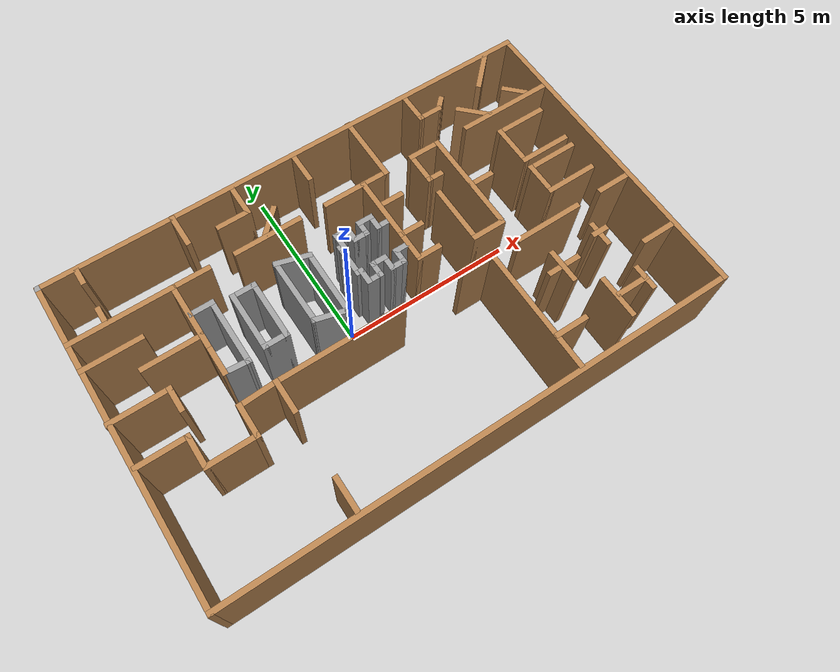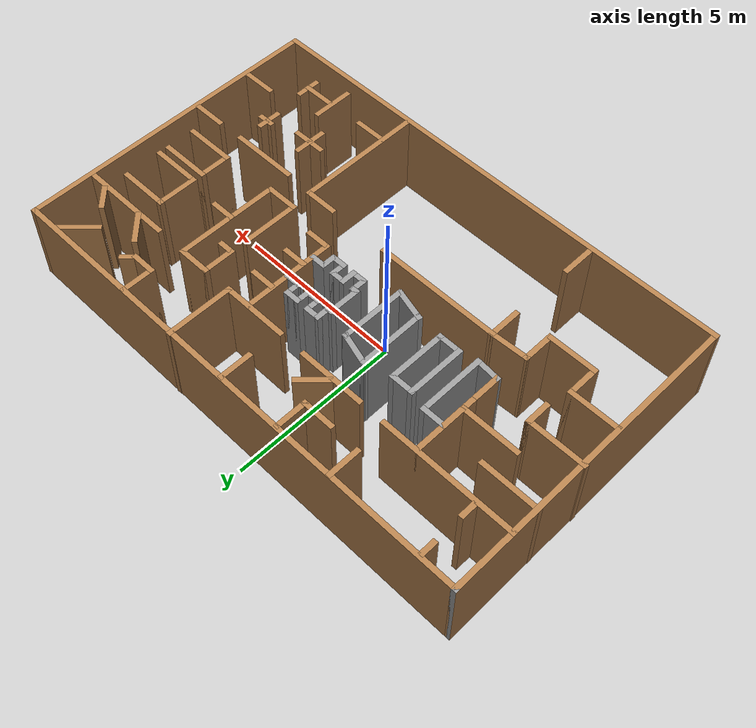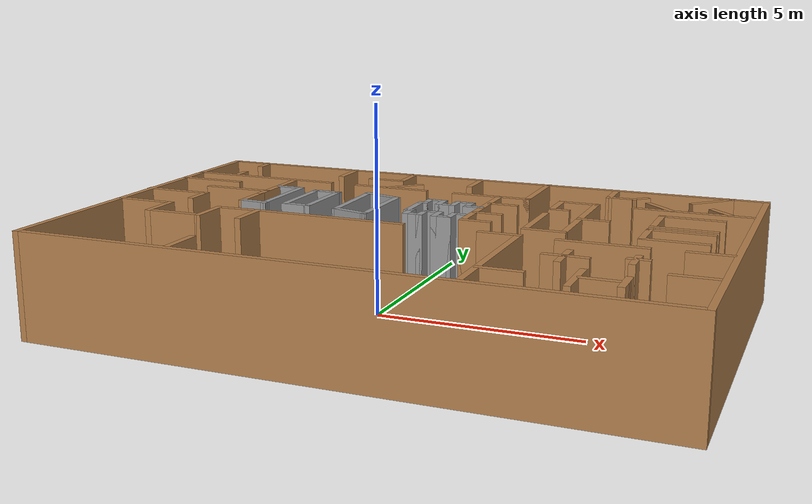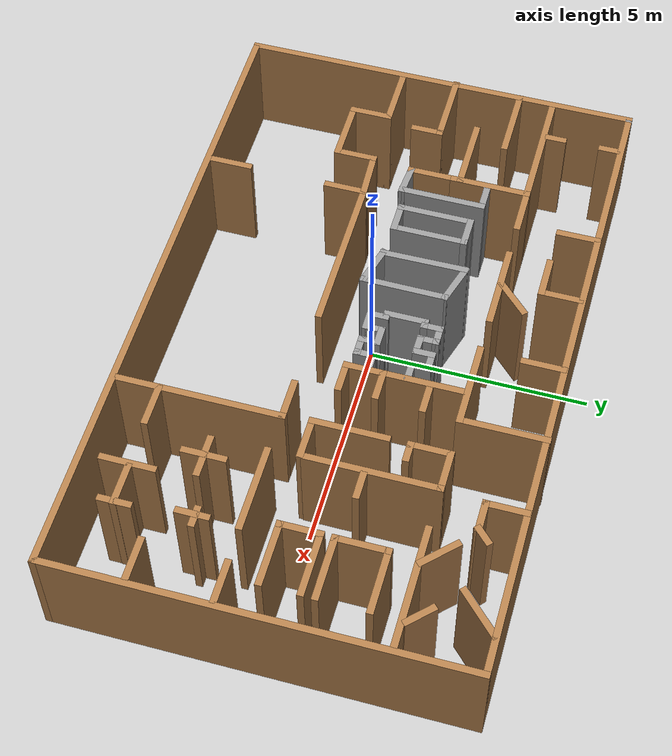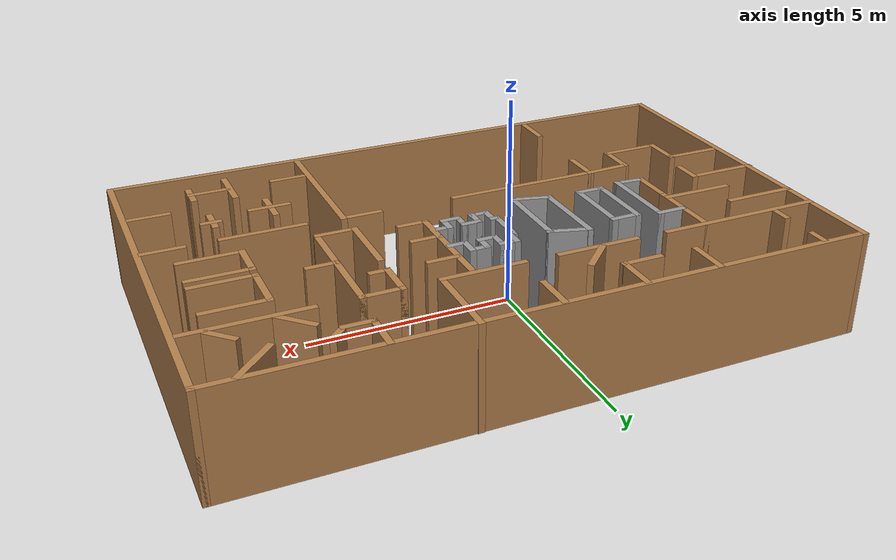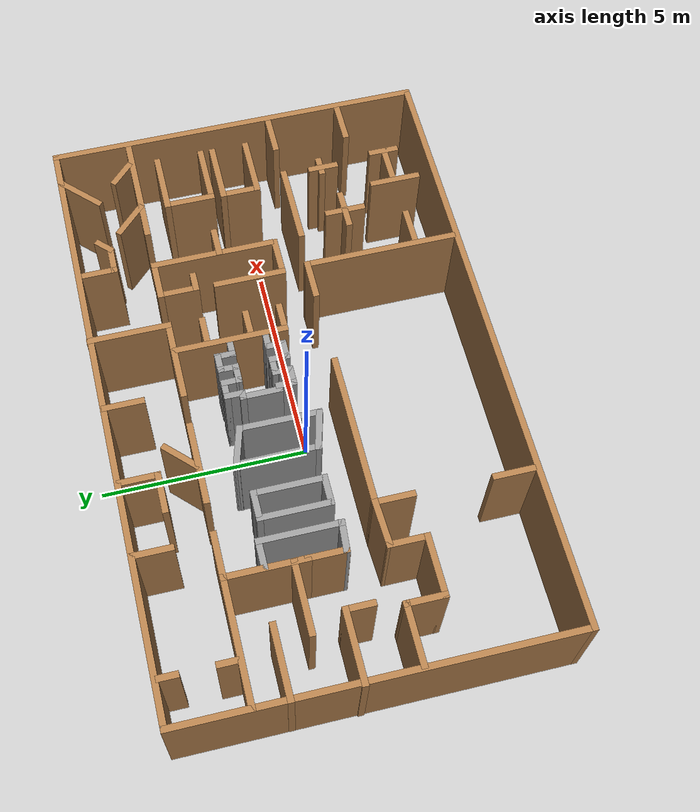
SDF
<?xml version='1.0'?>
<sdf version='1.6'>
  <model name='room'>
    <pose frame=''>0.8955 -0.0675 0 0 -0 0</pose>
    <link name='Wall_102'>
      <collision name='Wall_102_Collision'>
        <geometry>
          <box>
            <size>1.25 0.15 2.5</size>
          </box>
        </geometry>
        <pose frame=''>0 0 1.25 0 -0 0</pose>
      </collision>
      <visual name='Wall_102_Visual'>
        <pose frame=''>0 0 1.25 0 -0 0</pose>
        <geometry>
          <box>
            <size>1.25 0.15 2.5</size>
          </box>
        </geometry>
        <material>
          <script>
            <uri>file://media/materials/scripts/gazebo.material</uri>
            <name>Gazebo/Wood</name>
          </script>
          <ambient>1 1 1 1</ambient>
        </material>
        <meta>
          <layer>0</layer>
        </meta>
      </visual>
      <pose frame=''>6.0995 4.1165 0 0 -0 -2.35619</pose>
    </link>
    <link name='Wall_104'>
      <collision name='Wall_104_Collision'>
        <geometry>
          <box>
            <size>1 0.15 2.5</size>
          </box>
        </geometry>
        <pose frame=''>0 0 1.25 0 -0 0</pose>
      </collision>
      <visual name='Wall_104_Visual'>
        <pose frame=''>0 0 1.25 0 -0 0</pose>
        <geometry>
          <box>
            <size>1 0.15 2.5</size>
          </box>
        </geometry>
        <material>
          <script>
            <uri>file://media/materials/scripts/gazebo.material</uri>
            <name>Gazebo/Wood</name>
          </script>
          <ambient>1 1 1 1</ambient>
        </material>
        <meta>
          <layer>0</layer>
        </meta>
      </visual>
      <pose frame=''>5.044 3.057 0 0 -0 2.35619</pose>
    </link>
    <link name='Wall_107'>
      <collision name='Wall_107_Collision'>
        <geometry>
          <box>
            <size>0.75 0.15 2.5</size>
          </box>
        </geometry>
        <pose frame=''>0 0 1.25 0 -0 0</pose>
      </collision>
      <visual name='Wall_107_Visual'>
        <pose frame=''>0 0 1.25 0 -0 0</pose>
        <geometry>
          <box>
            <size>0.75 0.15 2.5</size>
          </box>
        </geometry>
        <material>
          <script>
            <uri>file://media/materials/scripts/gazebo.material</uri>
            <name>Gazebo/Wood</name>
          </script>
          <ambient>1 1 1 1</ambient>
        </material>
        <meta>
          <layer>0</layer>
        </meta>
      </visual>
      <pose frame=''>6.4485 3.0245 0 0 -0 -0.785398</pose>
    </link>
    <link name='Wall_11'>
      <collision name='Wall_11_Collision'>
        <geometry>
          <box>
            <size>0.5 0.15 2.5</size>
          </box>
        </geometry>
        <pose frame=''>0 0 1.25 0 -0 0</pose>
      </collision>
      <visual name='Wall_11_Visual'>
        <pose frame=''>0 0 1.25 0 -0 0</pose>
        <geometry>
          <box>
            <size>0.5 0.15 2.5</size>
          </box>
        </geometry>
        <material>
          <script>
            <uri>file://media/materials/scripts/gazebo.material</uri>
            <name>Gazebo/Wood</name>
          </script>
          <ambient>0.921569 0.807843 0.615686 1</ambient>
        </material>
        <meta>
          <layer>0</layer>
        </meta>
      </visual>
      <pose frame=''>-6.2495 4.2745 0 0 -0 1.5708</pose>
    </link>
    <link name='Wall_112'>
      <collision name='Wall_112_Collision'>
        <geometry>
          <box>
            <size>0.5 0.15 2.5</size>
          </box>
        </geometry>
        <pose frame=''>0 0 1.25 0 -0 0</pose>
      </collision>
      <visual name='Wall_112_Visual'>
        <pose frame=''>0 0 1.25 0 -0 0</pose>
        <geometry>
          <box>
            <size>0.5 0.15 2.5</size>
          </box>
        </geometry>
        <material>
          <script>
            <uri>file://media/materials/scripts/gazebo.material</uri>
            <name>Gazebo/Wood</name>
          </script>
          <ambient>1 1 1 1</ambient>
        </material>
        <meta>
          <layer>0</layer>
        </meta>
      </visual>
      <pose frame=''>2.9305 1.8815 0 0 -0 0</pose>
    </link>
    <link name='Wall_115'>
      <collision name='Wall_115_Collision'>
        <geometry>
          <box>
            <size>0.75 0.15 2.5</size>
          </box>
        </geometry>
        <pose frame=''>0 0 1.25 0 -0 0</pose>
      </collision>
      <visual name='Wall_115_Visual'>
        <pose frame=''>0 0 1.25 0 -0 0</pose>
        <geometry>
          <box>
            <size>0.75 0.15 2.5</size>
          </box>
        </geometry>
        <material>
          <script>
            <uri>file://media/materials/scripts/gazebo.material</uri>
            <name>Gazebo/Wood</name>
          </script>
          <ambient>1 1 1 1</ambient>
        </material>
        <meta>
          <layer>0</layer>
        </meta>
      </visual>
      <pose frame=''>3.9985 3.6755 0 0 -0 0</pose>
    </link>
    <link name='Wall_116'>
      <collision name='Wall_116_Collision'>
        <geometry>
          <box>
            <size>0.5 0.15 2.5</size>
          </box>
        </geometry>
        <pose frame=''>0 0 1.25 0 -0 0</pose>
      </collision>
      <visual name='Wall_116_Visual'>
        <pose frame=''>0 0 1.25 0 -0 0</pose>
        <geometry>
          <box>
            <size>0.5 0.15 2.5</size>
          </box>
        </geometry>
        <material>
          <script>
            <uri>file://media/materials/scripts/gazebo.material</uri>
            <name>Gazebo/Wood</name>
          </script>
          <ambient>1 1 1 1</ambient>
        </material>
        <meta>
          <layer>0</layer>
        </meta>
      </visual>
      <pose frame=''>4.422 3.799 0 0 -0 0.785398</pose>
    </link>
    <link name='Wall_118'>
      <collision name='Wall_118_Collision'>
        <geometry>
          <box>
            <size>2 0.15 2.5</size>
          </box>
        </geometry>
        <pose frame=''>0 0 1.25 0 -0 0</pose>
      </collision>
      <visual name='Wall_118_Visual'>
        <pose frame=''>0 0 1.25 0 -0 0</pose>
        <geometry>
          <box>
            <size>2 0.15 2.5</size>
          </box>
        </geometry>
        <material>
          <script>
            <uri>file://media/materials/scripts/gazebo.material</uri>
            <name>Gazebo/Grey</name>
          </script>
          <ambient>1 1 1 1</ambient>
        </material>
        <meta>
          <layer>0</layer>
        </meta>
      </visual>
      <pose frame=''>-1.93559 0.967643 0 0 -0 -1.56262</pose>
    </link>
    <link name='Wall_119'>
      <collision name='Wall_119_Collision'>
        <geometry>
          <box>
            <size>1 0.15 2.5</size>
          </box>
        </geometry>
        <pose frame=''>0 0 1.25 0 -0 0</pose>
      </collision>
      <visual name='Wall_119_Visual'>
        <pose frame=''>0 0 1.25 0 -0 0</pose>
        <geometry>
          <box>
            <size>1 0.15 2.5</size>
          </box>
        </geometry>
        <material>
          <script>
            <uri>file://media/materials/scripts/gazebo.material</uri>
            <name>Gazebo/Grey</name>
          </script>
          <ambient>1 1 1 1</ambient>
        </material>
        <meta>
          <layer>0</layer>
        </meta>
      </visual>
      <pose frame=''>-1.53264 -0.067355 0 0 -0 -0.261799</pose>
    </link>
    <link name='Wall_120'>
      <collision name='Wall_120_Collision'>
        <geometry>
          <box>
            <size>1.97005 0.15 2.5</size>
          </box>
        </geometry>
        <pose frame=''>0 0 1.25 0 -0 0</pose>
      </collision>
      <visual name='Wall_120_Visual'>
        <pose frame=''>0 0 1.25 0 -0 0</pose>
        <geometry>
          <box>
            <size>1.97005 0.15 2.5</size>
          </box>
        </geometry>
        <material>
          <script>
            <uri>file://media/materials/scripts/gazebo.material</uri>
            <name>Gazebo/Grey</name>
          </script>
          <ambient>1 1 1 1</ambient>
        </material>
        <meta>
          <layer>0</layer>
        </meta>
      </visual>
      <pose frame=''>-1.10008 0.732645 0 0 -0 1.56319</pose>
    </link>
    <link name='Wall_121'>
      <collision name='Wall_121_Collision'>
        <geometry>
          <box>
            <size>1.036 0.15 2.5</size>
          </box>
        </geometry>
        <pose frame=''>0 0 1.25 0 -0 0</pose>
      </collision>
      <visual name='Wall_121_Visual'>
        <pose frame=''>0 0 1.25 0 -0 0</pose>
        <geometry>
          <box>
            <size>1.036 0.15 2.5</size>
          </box>
        </geometry>
        <material>
          <script>
            <uri>file://media/materials/scripts/gazebo.material</uri>
            <name>Gazebo/Grey</name>
          </script>
          <ambient>1 1 1 1</ambient>
        </material>
        <meta>
          <layer>0</layer>
        </meta>
      </visual>
      <pose frame=''>-1.51816 1.78277 0 0 -0 2.85554</pose>
    </link>
    <link name='Wall_123'>
      <collision name='Wall_123_Collision'>
        <geometry>
          <box>
            <size>0.75 0.15 2.5</size>
          </box>
        </geometry>
        <pose frame=''>0 0 1.25 0 -0 0</pose>
      </collision>
      <visual name='Wall_123_Visual'>
        <pose frame=''>0 0 1.25 0 -0 0</pose>
        <geometry>
          <box>
            <size>0.75 0.15 2.5</size>
          </box>
        </geometry>
        <material>
          <script>
            <uri>file://media/materials/scripts/gazebo.material</uri>
            <name>Gazebo/Grey</name>
          </script>
          <ambient>1 1 1 1</ambient>
        </material>
        <meta>
          <layer>0</layer>
        </meta>
      </visual>
      <pose frame=''>-4.10944 1.82992 0 0 -0 0</pose>
    </link>
    <link name='Wall_124'>
      <collision name='Wall_124_Collision'>
        <geometry>
          <box>
            <size>2 0.15 2.5</size>
          </box>
        </geometry>
        <pose frame=''>0 0 1.25 0 -0 0</pose>
      </collision>
      <visual name='Wall_124_Visual'>
        <pose frame=''>0 0 1.25 0 -0 0</pose>
        <geometry>
          <box>
            <size>2 0.15 2.5</size>
          </box>
        </geometry>
        <material>
          <script>
            <uri>file://media/materials/scripts/gazebo.material</uri>
            <name>Gazebo/Grey</name>
          </script>
          <ambient>1 1 1 1</ambient>
        </material>
        <meta>
          <layer>0</layer>
        </meta>
      </visual>
      <pose frame=''>-3.80944 0.904922 0 0 -0 -1.5708</pose>
    </link>
    <link name='Wall_127'>
      <collision name='Wall_127_Collision'>
        <geometry>
          <box>
            <size>0.777182 0.15 2.5</size>
          </box>
        </geometry>
        <pose frame=''>0 0 1.25 0 -0 0</pose>
      </collision>
      <visual name='Wall_127_Visual'>
        <pose frame=''>0 0 1.25 0 -0 0</pose>
        <geometry>
          <box>
            <size>0.777182 0.15 2.5</size>
          </box>
        </geometry>
        <material>
          <script>
            <uri>file://media/materials/scripts/gazebo.material</uri>
            <name>Gazebo/Grey</name>
          </script>
          <ambient>1 1 1 1</ambient>
        </material>
        <meta>
          <layer>0</layer>
        </meta>
      </visual>
      <pose frame=''>-4.12197 0.005711 0 0 -0 -0.082331</pose>
    </link>
    <link name='Wall_129'>
      <collision name='Wall_129_Collision'>
        <geometry>
          <box>
            <size>1.75 0.15 2.5</size>
          </box>
        </geometry>
        <pose frame=''>0 0 1.25 0 -0 0</pose>
      </collision>
      <visual name='Wall_129_Visual'>
        <pose frame=''>0 0 1.25 0 -0 0</pose>
        <geometry>
          <box>
            <size>1.75 0.15 2.5</size>
          </box>
        </geometry>
        <material>
          <script>
            <uri>file://media/materials/scripts/gazebo.material</uri>
            <name>Gazebo/Grey</name>
          </script>
          <ambient>1 1 1 1</ambient>
        </material>
        <meta>
          <layer>0</layer>
        </meta>
      </visual>
      <pose frame=''>-3.29698 0.889465 0 0 -0 -1.5708</pose>
    </link>
    <link name='Wall_13'>
      <collision name='Wall_13_Collision'>
        <geometry>
          <box>
            <size>0.5 0.15 2.5</size>
          </box>
        </geometry>
        <pose frame=''>0 0 1.25 0 -0 0</pose>
      </collision>
      <visual name='Wall_13_Visual'>
        <pose frame=''>0 0 1.25 0 -0 0</pose>
        <geometry>
          <box>
            <size>0.5 0.15 2.5</size>
          </box>
        </geometry>
        <material>
          <script>
            <uri>file://media/materials/scripts/gazebo.material</uri>
            <name>Gazebo/Wood</name>
          </script>
          <ambient>0.921569 0.807843 0.615686 1</ambient>
        </material>
        <meta>
          <layer>0</layer>
        </meta>
      </visual>
      <pose frame=''>-6.2495 3.0165 0 0 -0 -1.5708</pose>
    </link>
    <link name='Wall_130'>
      <collision name='Wall_130_Collision'>
        <geometry>
          <box>
            <size>0.75 0.15 2.5</size>
          </box>
        </geometry>
        <pose frame=''>0 0 1.25 0 -0 0</pose>
      </collision>
      <visual name='Wall_130_Visual'>
        <pose frame=''>0 0 1.25 0 -0 0</pose>
        <geometry>
          <box>
            <size>0.75 0.15 2.5</size>
          </box>
        </geometry>
        <material>
          <script>
            <uri>file://media/materials/scripts/gazebo.material</uri>
            <name>Gazebo/Grey</name>
          </script>
          <ambient>1 1 1 1</ambient>
        </material>
        <meta>
          <layer>0</layer>
        </meta>
      </visual>
      <pose frame=''>-2.99698 0.089465 0 0 -0 0</pose>
    </link>
    <link name='Wall_131'>
      <collision name='Wall_131_Collision'>
        <geometry>
          <box>
            <size>1.75 0.15 2.5</size>
          </box>
        </geometry>
        <pose frame=''>0 0 1.25 0 -0 0</pose>
      </collision>
      <visual name='Wall_131_Visual'>
        <pose frame=''>0 0 1.25 0 -0 0</pose>
        <geometry>
          <box>
            <size>1.75 0.15 2.5</size>
          </box>
        </geometry>
        <material>
          <script>
            <uri>file://media/materials/scripts/gazebo.material</uri>
            <name>Gazebo/Grey</name>
          </script>
          <ambient>1 1 1 1</ambient>
        </material>
        <meta>
          <layer>0</layer>
        </meta>
      </visual>
      <pose frame=''>-2.69698 0.889465 0 0 -0 1.5708</pose>
    </link>
    <link name='Wall_132'>
      <collision name='Wall_132_Collision'>
        <geometry>
          <box>
            <size>0.75 0.15 2.5</size>
          </box>
        </geometry>
        <pose frame=''>0 0 1.25 0 -0 0</pose>
      </collision>
      <visual name='Wall_132_Visual'>
        <pose frame=''>0 0 1.25 0 -0 0</pose>
        <geometry>
          <box>
            <size>0.75 0.15 2.5</size>
          </box>
        </geometry>
        <material>
          <script>
            <uri>file://media/materials/scripts/gazebo.material</uri>
            <name>Gazebo/Grey</name>
          </script>
          <ambient>1 1 1 1</ambient>
        </material>
        <meta>
          <layer>0</layer>
        </meta>
      </visual>
      <pose frame=''>-2.99698 1.68946 0 0 -0 3.14159</pose>
    </link>
    <link name='Wall_134'>
      <collision name='Wall_134_Collision'>
        <geometry>
          <box>
            <size>0.5 0.15 2.5</size>
          </box>
        </geometry>
        <pose frame=''>0 0 1.25 0 -0 0</pose>
      </collision>
      <visual name='Wall_134_Visual'>
        <pose frame=''>0 0 1.25 0 -0 0</pose>
        <geometry>
          <box>
            <size>0.5 0.15 2.5</size>
          </box>
        </geometry>
        <material>
          <script>
            <uri>file://media/materials/scripts/gazebo.material</uri>
            <name>Gazebo/Grey</name>
          </script>
          <ambient>1 1 1 1</ambient>
        </material>
        <meta>
          <layer>0</layer>
        </meta>
      </visual>
      <pose frame=''>-0.236104 1.58364 0 0 -0 -1.5708</pose>
    </link>
    <link name='Wall_135'>
      <collision name='Wall_135_Collision'>
        <geometry>
          <box>
            <size>0.25 0.15 2.5</size>
          </box>
        </geometry>
        <pose frame=''>0 0 1.25 0 -0 0</pose>
      </collision>
      <visual name='Wall_135_Visual'>
        <pose frame=''>0 0 1.25 0 -0 0</pose>
        <geometry>
          <box>
            <size>0.25 0.15 2.5</size>
          </box>
        </geometry>
        <material>
          <script>
            <uri>file://media/materials/scripts/gazebo.material</uri>
            <name>Gazebo/Grey</name>
          </script>
          <ambient>1 1 1 1</ambient>
        </material>
        <meta>
          <layer>0</layer>
        </meta>
      </visual>
      <pose frame=''>-0.286104 1.40864 0 0 -0 3.14159</pose>
    </link>
    <link name='Wall_136'>
      <collision name='Wall_136_Collision'>
        <geometry>
          <box>
            <size>1 0.15 2.5</size>
          </box>
        </geometry>
        <pose frame=''>0 0 1.25 0 -0 0</pose>
      </collision>
      <visual name='Wall_136_Visual'>
        <pose frame=''>0 0 1.25 0 -0 0</pose>
        <geometry>
          <box>
            <size>1 0.15 2.5</size>
          </box>
        </geometry>
        <material>
          <script>
            <uri>file://media/materials/scripts/gazebo.material</uri>
            <name>Gazebo/Grey</name>
          </script>
          <ambient>1 1 1 1</ambient>
        </material>
        <meta>
          <layer>0</layer>
        </meta>
      </visual>
      <pose frame=''>-0.336104 0.983637 0 0 -0 -1.5708</pose>
    </link>
    <link name='Wall_137'>
      <collision name='Wall_137_Collision'>
        <geometry>
          <box>
            <size>0.25 0.15 2.5</size>
          </box>
        </geometry>
        <pose frame=''>0 0 1.25 0 -0 0</pose>
      </collision>
      <visual name='Wall_137_Visual'>
        <pose frame=''>0 0 1.25 0 -0 0</pose>
        <geometry>
          <box>
            <size>0.25 0.15 2.5</size>
          </box>
        </geometry>
        <material>
          <script>
            <uri>file://media/materials/scripts/gazebo.material</uri>
            <name>Gazebo/Grey</name>
          </script>
          <ambient>1 1 1 1</ambient>
        </material>
        <meta>
          <layer>0</layer>
        </meta>
      </visual>
      <pose frame=''>-0.286104 0.558637 0 0 -0 0</pose>
    </link>
    <link name='Wall_138'>
      <collision name='Wall_138_Collision'>
        <geometry>
          <box>
            <size>0.5 0.15 2.5</size>
          </box>
        </geometry>
        <pose frame=''>0 0 1.25 0 -0 0</pose>
      </collision>
      <visual name='Wall_138_Visual'>
        <pose frame=''>0 0 1.25 0 -0 0</pose>
        <geometry>
          <box>
            <size>0.5 0.15 2.5</size>
          </box>
        </geometry>
        <material>
          <script>
            <uri>file://media/materials/scripts/gazebo.material</uri>
            <name>Gazebo/Grey</name>
          </script>
          <ambient>1 1 1 1</ambient>
        </material>
        <meta>
          <layer>0</layer>
        </meta>
      </visual>
      <pose frame=''>-0.236104 0.383637 0 0 -0 -1.5708</pose>
    </link>
    <link name='Wall_139'>
      <collision name='Wall_139_Collision'>
        <geometry>
          <box>
            <size>0.5 0.15 2.5</size>
          </box>
        </geometry>
        <pose frame=''>0 0 1.25 0 -0 0</pose>
      </collision>
      <visual name='Wall_139_Visual'>
        <pose frame=''>0 0 1.25 0 -0 0</pose>
        <geometry>
          <box>
            <size>0.5 0.15 2.5</size>
          </box>
        </geometry>
        <material>
          <script>
            <uri>file://media/materials/scripts/gazebo.material</uri>
            <name>Gazebo/Grey</name>
          </script>
          <ambient>1 1 1 1</ambient>
        </material>
        <meta>
          <layer>0</layer>
        </meta>
      </visual>
      <pose frame=''>-0.061104 0.208637 0 0 -0 0</pose>
    </link>
    <link name='Wall_140'>
      <collision name='Wall_140_Collision'>
        <geometry>
          <box>
            <size>0.5 0.15 2.5</size>
          </box>
        </geometry>
        <pose frame=''>0 0 1.25 0 -0 0</pose>
      </collision>
      <visual name='Wall_140_Visual'>
        <pose frame=''>0 0 1.25 0 -0 0</pose>
        <geometry>
          <box>
            <size>0.5 0.15 2.5</size>
          </box>
        </geometry>
        <material>
          <script>
            <uri>file://media/materials/scripts/gazebo.material</uri>
            <name>Gazebo/Grey</name>
          </script>
          <ambient>1 1 1 1</ambient>
        </material>
        <meta>
          <layer>0</layer>
        </meta>
      </visual>
      <pose frame=''>0.113896 0.383637 0 0 -0 1.5708</pose>
    </link>
    <link name='Wall_141'>
      <collision name='Wall_141_Collision'>
        <geometry>
          <box>
            <size>0.5 0.15 2.5</size>
          </box>
        </geometry>
        <pose frame=''>0 0 1.25 0 -0 0</pose>
      </collision>
      <visual name='Wall_141_Visual'>
        <pose frame=''>0 0 1.25 0 -0 0</pose>
        <geometry>
          <box>
            <size>0.5 0.15 2.5</size>
          </box>
        </geometry>
        <material>
          <script>
            <uri>file://media/materials/scripts/gazebo.material</uri>
            <name>Gazebo/Grey</name>
          </script>
          <ambient>1 1 1 1</ambient>
        </material>
        <meta>
          <layer>0</layer>
        </meta>
      </visual>
      <pose frame=''>0.288896 0.558637 0 0 -0 0</pose>
    </link>
    <link name='Wall_142'>
      <collision name='Wall_142_Collision'>
        <geometry>
          <box>
            <size>0.5 0.15 2.5</size>
          </box>
        </geometry>
        <pose frame=''>0 0 1.25 0 -0 0</pose>
      </collision>
      <visual name='Wall_142_Visual'>
        <pose frame=''>0 0 1.25 0 -0 0</pose>
        <geometry>
          <box>
            <size>0.5 0.15 2.5</size>
          </box>
        </geometry>
        <material>
          <script>
            <uri>file://media/materials/scripts/gazebo.material</uri>
            <name>Gazebo/Grey</name>
          </script>
          <ambient>1 1 1 1</ambient>
        </material>
        <meta>
          <layer>0</layer>
        </meta>
      </visual>
      <pose frame=''>0.463896 0.383637 0 0 -0 -1.5708</pose>
    </link>
    <link name='Wall_143'>
      <collision name='Wall_143_Collision'>
        <geometry>
          <box>
            <size>0.5 0.15 2.5</size>
          </box>
        </geometry>
        <pose frame=''>0 0 1.25 0 -0 0</pose>
      </collision>
      <visual name='Wall_143_Visual'>
        <pose frame=''>0 0 1.25 0 -0 0</pose>
        <geometry>
          <box>
            <size>0.5 0.15 2.5</size>
          </box>
        </geometry>
        <material>
          <script>
            <uri>file://media/materials/scripts/gazebo.material</uri>
            <name>Gazebo/Grey</name>
          </script>
          <ambient>1 1 1 1</ambient>
        </material>
        <meta>
          <layer>0</layer>
        </meta>
      </visual>
      <pose frame=''>0.638896 0.208637 0 0 -0 0</pose>
    </link>
    <link name='Wall_144'>
      <collision name='Wall_144_Collision'>
        <geometry>
          <box>
            <size>0.5 0.15 2.5</size>
          </box>
        </geometry>
        <pose frame=''>0 0 1.25 0 -0 0</pose>
      </collision>
      <visual name='Wall_144_Visual'>
        <pose frame=''>0 0 1.25 0 -0 0</pose>
        <geometry>
          <box>
            <size>0.5 0.15 2.5</size>
          </box>
        </geometry>
        <material>
          <script>
            <uri>file://media/materials/scripts/gazebo.material</uri>
            <name>Gazebo/Grey</name>
          </script>
          <ambient>1 1 1 1</ambient>
        </material>
        <meta>
          <layer>0</layer>
        </meta>
      </visual>
      <pose frame=''>0.813896 0.383637 0 0 -0 1.5708</pose>
    </link>
    <link name='Wall_145'>
      <collision name='Wall_145_Collision'>
        <geometry>
          <box>
            <size>0.5 0.15 2.5</size>
          </box>
        </geometry>
        <pose frame=''>0 0 1.25 0 -0 0</pose>
      </collision>
      <visual name='Wall_145_Visual'>
        <pose frame=''>0 0 1.25 0 -0 0</pose>
        <geometry>
          <box>
            <size>0.5 0.15 2.5</size>
          </box>
        </geometry>
        <material>
          <script>
            <uri>file://media/materials/scripts/gazebo.material</uri>
            <name>Gazebo/Grey</name>
          </script>
          <ambient>1 1 1 1</ambient>
        </material>
        <meta>
          <layer>0</layer>
        </meta>
      </visual>
      <pose frame=''>0.988896 0.558637 0 0 -0 0</pose>
    </link>
    <link name='Wall_147'>
      <collision name='Wall_147_Collision'>
        <geometry>
          <box>
            <size>0.5 0.15 2.5</size>
          </box>
        </geometry>
        <pose frame=''>0 0 1.25 0 -0 0</pose>
      </collision>
      <visual name='Wall_147_Visual'>
        <pose frame=''>0 0 1.25 0 -0 0</pose>
        <geometry>
          <box>
            <size>0.5 0.15 2.5</size>
          </box>
        </geometry>
        <material>
          <script>
            <uri>file://media/materials/scripts/gazebo.material</uri>
            <name>Gazebo/Grey</name>
          </script>
          <ambient>1 1 1 1</ambient>
        </material>
        <meta>
          <layer>0</layer>
        </meta>
      </visual>
      <pose frame=''>-0.061104 1.75864 0 0 -0 0</pose>
    </link>
    <link name='Wall_148'>
      <collision name='Wall_148_Collision'>
        <geometry>
          <box>
            <size>0.5 0.15 2.5</size>
          </box>
        </geometry>
        <pose frame=''>0 0 1.25 0 -0 0</pose>
      </collision>
      <visual name='Wall_148_Visual'>
        <pose frame=''>0 0 1.25 0 -0 0</pose>
        <geometry>
          <box>
            <size>0.5 0.15 2.5</size>
          </box>
        </geometry>
        <material>
          <script>
            <uri>file://media/materials/scripts/gazebo.material</uri>
            <name>Gazebo/Grey</name>
          </script>
          <ambient>1 1 1 1</ambient>
        </material>
        <meta>
          <layer>0</layer>
        </meta>
      </visual>
      <pose frame=''>0.113896 1.58364 0 0 -0 -1.5708</pose>
    </link>
    <link name='Wall_149'>
      <collision name='Wall_149_Collision'>
        <geometry>
          <box>
            <size>0.5 0.15 2.5</size>
          </box>
        </geometry>
        <pose frame=''>0 0 1.25 0 -0 0</pose>
      </collision>
      <visual name='Wall_149_Visual'>
        <pose frame=''>0 0 1.25 0 -0 0</pose>
        <geometry>
          <box>
            <size>0.5 0.15 2.5</size>
          </box>
        </geometry>
        <material>
          <script>
            <uri>file://media/materials/scripts/gazebo.material</uri>
            <name>Gazebo/Grey</name>
          </script>
          <ambient>1 1 1 1</ambient>
        </material>
        <meta>
          <layer>0</layer>
        </meta>
      </visual>
      <pose frame=''>0.288896 1.40864 0 0 -0 0</pose>
    </link>
    <link name='Wall_15'>
      <collision name='Wall_15_Collision'>
        <geometry>
          <box>
            <size>4 0.15 2.5</size>
          </box>
        </geometry>
        <pose frame=''>0 0 1.25 0 -0 0</pose>
      </collision>
      <visual name='Wall_15_Visual'>
        <pose frame=''>0 0 1.25 0 -0 0</pose>
        <geometry>
          <box>
            <size>4 0.15 2.5</size>
          </box>
        </geometry>
        <material>
          <script>
            <uri>file://media/materials/scripts/gazebo.material</uri>
            <name>Gazebo/Wood</name>
          </script>
          <ambient>0.921569 0.807843 0.615686 1</ambient>
        </material>
        <meta>
          <layer>0</layer>
        </meta>
      </visual>
      <pose frame=''>-5.3595 2.7315 0 0 -0 0</pose>
    </link>
    <link name='Wall_150'>
      <collision name='Wall_150_Collision'>
        <geometry>
          <box>
            <size>0.5 0.15 2.5</size>
          </box>
        </geometry>
        <pose frame=''>0 0 1.25 0 -0 0</pose>
      </collision>
      <visual name='Wall_150_Visual'>
        <pose frame=''>0 0 1.25 0 -0 0</pose>
        <geometry>
          <box>
            <size>0.5 0.15 2.5</size>
          </box>
        </geometry>
        <material>
          <script>
            <uri>file://media/materials/scripts/gazebo.material</uri>
            <name>Gazebo/Grey</name>
          </script>
          <ambient>1 1 1 1</ambient>
        </material>
        <meta>
          <layer>0</layer>
        </meta>
      </visual>
      <pose frame=''>0.463896 1.58364 0 0 -0 1.5708</pose>
    </link>
    <link name='Wall_151'>
      <collision name='Wall_151_Collision'>
        <geometry>
          <box>
            <size>0.5 0.15 2.5</size>
          </box>
        </geometry>
        <pose frame=''>0 0 1.25 0 -0 0</pose>
      </collision>
      <visual name='Wall_151_Visual'>
        <pose frame=''>0 0 1.25 0 -0 0</pose>
        <geometry>
          <box>
            <size>0.5 0.15 2.5</size>
          </box>
        </geometry>
        <material>
          <script>
            <uri>file://media/materials/scripts/gazebo.material</uri>
            <name>Gazebo/Grey</name>
          </script>
          <ambient>1 1 1 1</ambient>
        </material>
        <meta>
          <layer>0</layer>
        </meta>
      </visual>
      <pose frame=''>0.638896 1.75864 0 0 -0 0</pose>
    </link>
    <link name='Wall_152'>
      <collision name='Wall_152_Collision'>
        <geometry>
          <box>
            <size>0.5 0.15 2.5</size>
          </box>
        </geometry>
        <pose frame=''>0 0 1.25 0 -0 0</pose>
      </collision>
      <visual name='Wall_152_Visual'>
        <pose frame=''>0 0 1.25 0 -0 0</pose>
        <geometry>
          <box>
            <size>0.5 0.15 2.5</size>
          </box>
        </geometry>
        <material>
          <script>
            <uri>file://media/materials/scripts/gazebo.material</uri>
            <name>Gazebo/Grey</name>
          </script>
          <ambient>1 1 1 1</ambient>
        </material>
        <meta>
          <layer>0</layer>
        </meta>
      </visual>
      <pose frame=''>0.813896 1.58364 0 0 -0 -1.5708</pose>
    </link>
    <link name='Wall_153'>
      <collision name='Wall_153_Collision'>
        <geometry>
          <box>
            <size>0.5 0.15 2.5</size>
          </box>
        </geometry>
        <pose frame=''>0 0 1.25 0 -0 0</pose>
      </collision>
      <visual name='Wall_153_Visual'>
        <pose frame=''>0 0 1.25 0 -0 0</pose>
        <geometry>
          <box>
            <size>0.5 0.15 2.5</size>
          </box>
        </geometry>
        <material>
          <script>
            <uri>file://media/materials/scripts/gazebo.material</uri>
            <name>Gazebo/Grey</name>
          </script>
          <ambient>1 1 1 1</ambient>
        </material>
        <meta>
          <layer>0</layer>
        </meta>
      </visual>
      <pose frame=''>0.988896 1.40864 0 0 -0 0</pose>
    </link>
    <link name='Wall_157'>
      <collision name='Wall_157_Collision'>
        <geometry>
          <box>
            <size>1.17417 0.15 2.5</size>
          </box>
        </geometry>
        <pose frame=''>0 0 1.25 0 -0 0</pose>
      </collision>
      <visual name='Wall_157_Visual'>
        <pose frame=''>0 0 1.25 0 -0 0</pose>
        <geometry>
          <box>
            <size>1.17417 0.15 2.5</size>
          </box>
        </geometry>
        <material>
          <script>
            <uri>file://media/materials/scripts/gazebo.material</uri>
            <name>Gazebo/Wood</name>
          </script>
          <ambient>1 1 1 1</ambient>
        </material>
        <meta>
          <layer>0</layer>
        </meta>
      </visual>
      <pose frame=''>-4.027 -0.868 0 0 -0 -3.09373</pose>
    </link>
    <link name='Wall_159'>
      <collision name='Wall_159_Collision'>
        <geometry>
          <box>
            <size>1 0.15 2.5</size>
          </box>
        </geometry>
        <pose frame=''>0 0 1.25 0 -0 0</pose>
      </collision>
      <visual name='Wall_159_Visual'>
        <pose frame=''>0 0 1.25 0 -0 0</pose>
        <geometry>
          <box>
            <size>1 0.15 2.5</size>
          </box>
        </geometry>
        <material>
          <script>
            <uri>file://media/materials/scripts/gazebo.material</uri>
            <name>Gazebo/Wood</name>
          </script>
          <ambient>1 1 1 1</ambient>
        </material>
        <meta>
          <layer>0</layer>
        </meta>
      </visual>
      <pose frame=''>-3.5155 -1.2685 0 0 -0 -1.5708</pose>
    </link>
    <link name='Wall_161'>
      <collision name='Wall_161_Collision'>
        <geometry>
          <box>
            <size>1 0.15 2.5</size>
          </box>
        </geometry>
        <pose frame=''>0 0 1.25 0 -0 0</pose>
      </collision>
      <visual name='Wall_161_Visual'>
        <pose frame=''>0 0 1.25 0 -0 0</pose>
        <geometry>
          <box>
            <size>1 0.15 2.5</size>
          </box>
        </geometry>
        <material>
          <script>
            <uri>file://media/materials/scripts/gazebo.material</uri>
            <name>Gazebo/Wood</name>
          </script>
          <ambient>1 1 1 1</ambient>
        </material>
        <meta>
          <layer>0</layer>
        </meta>
      </visual>
      <pose frame=''>-3.5405 -4.0025 0 0 -0 -1.5708</pose>
    </link>
    <link name='Wall_163'>
      <collision name='Wall_163_Collision'>
        <geometry>
          <box>
            <size>1.75 0.15 2.5</size>
          </box>
        </geometry>
        <pose frame=''>0 0 1.25 0 -0 0</pose>
      </collision>
      <visual name='Wall_163_Visual'>
        <pose frame=''>0 0 1.25 0 -0 0</pose>
        <geometry>
          <box>
            <size>1.75 0.15 2.5</size>
          </box>
        </geometry>
        <material>
          <script>
            <uri>file://media/materials/scripts/gazebo.material</uri>
            <name>Gazebo/Wood</name>
          </script>
          <ambient>1 1 1 1</ambient>
        </material>
        <meta>
          <layer>0</layer>
        </meta>
      </visual>
      <pose frame=''>-6.4885 1.9325 0 0 -0 0</pose>
    </link>
    <link name='Wall_165'>
      <collision name='Wall_165_Collision'>
        <geometry>
          <box>
            <size>1.75 0.15 2.5</size>
          </box>
        </geometry>
        <pose frame=''>0 0 1.25 0 -0 0</pose>
      </collision>
      <visual name='Wall_165_Visual'>
        <pose frame=''>0 0 1.25 0 -0 0</pose>
        <geometry>
          <box>
            <size>1.75 0.15 2.5</size>
          </box>
        </geometry>
        <material>
          <script>
            <uri>file://media/materials/scripts/gazebo.material</uri>
            <name>Gazebo/Wood</name>
          </script>
          <ambient>1 1 1 1</ambient>
        </material>
        <meta>
          <layer>0</layer>
        </meta>
      </visual>
      <pose frame=''>-5.2475 1.1825 0 0 -0 3.14159</pose>
    </link>
    <link name='Wall_167'>
      <collision name='Wall_167_Collision'>
        <geometry>
          <box>
            <size>1.75 0.15 2.5</size>
          </box>
        </geometry>
        <pose frame=''>0 0 1.25 0 -0 0</pose>
      </collision>
      <visual name='Wall_167_Visual'>
        <pose frame=''>0 0 1.25 0 -0 0</pose>
        <geometry>
          <box>
            <size>1.75 0.15 2.5</size>
          </box>
        </geometry>
        <material>
          <script>
            <uri>file://media/materials/scripts/gazebo.material</uri>
            <name>Gazebo/Wood</name>
          </script>
          <ambient>1 1 1 1</ambient>
        </material>
        <meta>
          <layer>0</layer>
        </meta>
      </visual>
      <pose frame=''>-6.5145 0.3805 0 0 -0 0</pose>
    </link>
    <link name='Wall_169'>
      <collision name='Wall_169_Collision'>
        <geometry>
          <box>
            <size>0.75 0.15 2.5</size>
          </box>
        </geometry>
        <pose frame=''>0 0 1.25 0 -0 0</pose>
      </collision>
      <visual name='Wall_169_Visual'>
        <pose frame=''>0 0 1.25 0 -0 0</pose>
        <geometry>
          <box>
            <size>0.75 0.15 2.5</size>
          </box>
        </geometry>
        <material>
          <script>
            <uri>file://media/materials/scripts/gazebo.material</uri>
            <name>Gazebo/Wood</name>
          </script>
          <ambient>1 1 1 1</ambient>
        </material>
        <meta>
          <layer>0</layer>
        </meta>
      </visual>
      <pose frame=''>-5.7145 0.0805 0 0 -0 -1.5708</pose>
    </link>
    <link name='Wall_17'>
      <collision name='Wall_17_Collision'>
        <geometry>
          <box>
            <size>1 0.15 2.5</size>
          </box>
        </geometry>
        <pose frame=''>0 0 1.25 0 -0 0</pose>
      </collision>
      <visual name='Wall_17_Visual'>
        <pose frame=''>0 0 1.25 0 -0 0</pose>
        <geometry>
          <box>
            <size>1 0.15 2.5</size>
          </box>
        </geometry>
        <material>
          <script>
            <uri>file://media/materials/scripts/gazebo.material</uri>
            <name>Gazebo/Wood</name>
          </script>
          <ambient>0.921569 0.807843 0.615686 1</ambient>
        </material>
        <meta>
          <layer>0</layer>
        </meta>
      </visual>
      <pose frame=''>-3.5235 4.1005 0 0 -0 -1.5708</pose>
    </link>
    <link name='Wall_171'>
      <collision name='Wall_171_Collision'>
        <geometry>
          <box>
            <size>1 0.15 2.5</size>
          </box>
        </geometry>
        <pose frame=''>0 0 1.25 0 -0 0</pose>
      </collision>
      <visual name='Wall_171_Visual'>
        <pose frame=''>0 0 1.25 0 -0 0</pose>
        <geometry>
          <box>
            <size>1 0.15 2.5</size>
          </box>
        </geometry>
        <material>
          <script>
            <uri>file://media/materials/scripts/gazebo.material</uri>
            <name>Gazebo/Wood</name>
          </script>
          <ambient>1 1 1 1</ambient>
        </material>
        <meta>
          <layer>0</layer>
        </meta>
      </visual>
      <pose frame=''>4.1435 -2.1045 0 0 -0 0</pose>
    </link>
    <link name='Wall_173'>
      <collision name='Wall_173_Collision'>
        <geometry>
          <box>
            <size>1 0.15 2.5</size>
          </box>
        </geometry>
        <pose frame=''>0 0 1.25 0 -0 0</pose>
      </collision>
      <visual name='Wall_173_Visual'>
        <pose frame=''>0 0 1.25 0 -0 0</pose>
        <geometry>
          <box>
            <size>1 0.15 2.5</size>
          </box>
        </geometry>
        <material>
          <script>
            <uri>file://media/materials/scripts/gazebo.material</uri>
            <name>Gazebo/Wood</name>
          </script>
          <ambient>1 1 1 1</ambient>
        </material>
        <meta>
          <layer>0</layer>
        </meta>
      </visual>
      <pose frame=''>4.1125 -2.1085 0 0 -0 -1.5708</pose>
    </link>
    <link name='Wall_175'>
      <collision name='Wall_175_Collision'>
        <geometry>
          <box>
            <size>1 0.15 2.5</size>
          </box>
        </geometry>
        <pose frame=''>0 0 1.25 0 -0 0</pose>
      </collision>
      <visual name='Wall_175_Visual'>
        <pose frame=''>0 0 1.25 0 -0 0</pose>
        <geometry>
          <box>
            <size>1 0.15 2.5</size>
          </box>
        </geometry>
        <material>
          <script>
            <uri>file://media/materials/scripts/gazebo.material</uri>
            <name>Gazebo/Wood</name>
          </script>
          <ambient>1 1 1 1</ambient>
        </material>
        <meta>
          <layer>0</layer>
        </meta>
      </visual>
      <pose frame=''>5.2215 -3.4985 0 0 -0 0</pose>
    </link>
    <link name='Wall_177'>
      <collision name='Wall_177_Collision'>
        <geometry>
          <box>
            <size>1.25 0.15 2.5</size>
          </box>
        </geometry>
        <pose frame=''>0 0 1.25 0 -0 0</pose>
      </collision>
      <visual name='Wall_177_Visual'>
        <pose frame=''>0 0 1.25 0 -0 0</pose>
        <geometry>
          <box>
            <size>1.25 0.15 2.5</size>
          </box>
        </geometry>
        <material>
          <script>
            <uri>file://media/materials/scripts/gazebo.material</uri>
            <name>Gazebo/Wood</name>
          </script>
          <ambient>1 1 1 1</ambient>
        </material>
        <meta>
          <layer>0</layer>
        </meta>
      </visual>
      <pose frame=''>4.7175 -3.5355 0 0 -0 -1.5708</pose>
    </link>
    <link name='Wall_179'>
      <collision name='Wall_179_Collision'>
        <geometry>
          <box>
            <size>0.75 0.15 2.5</size>
          </box>
        </geometry>
        <pose frame=''>0 0 1.25 0 -0 0</pose>
      </collision>
      <visual name='Wall_179_Visual'>
        <pose frame=''>0 0 1.25 0 -0 0</pose>
        <geometry>
          <box>
            <size>0.75 0.15 2.5</size>
          </box>
        </geometry>
        <material>
          <script>
            <uri>file://media/materials/scripts/gazebo.material</uri>
            <name>Gazebo/Wood</name>
          </script>
          <ambient>1 1 1 1</ambient>
        </material>
        <meta>
          <layer>0</layer>
        </meta>
      </visual>
      <pose frame=''>5.6385 -3.4835 0 0 -0 -1.5708</pose>
    </link>
    <link name='Wall_181'>
      <collision name='Wall_181_Collision'>
        <geometry>
          <box>
            <size>0.5 0.15 2.5</size>
          </box>
        </geometry>
        <pose frame=''>0 0 1.25 0 -0 0</pose>
      </collision>
      <visual name='Wall_181_Visual'>
        <pose frame=''>0 0 1.25 0 -0 0</pose>
        <geometry>
          <box>
            <size>0.5 0.15 2.5</size>
          </box>
        </geometry>
        <material>
          <script>
            <uri>file://media/materials/scripts/gazebo.material</uri>
            <name>Gazebo/Wood</name>
          </script>
          <ambient>1 1 1 1</ambient>
        </material>
        <meta>
          <layer>0</layer>
        </meta>
      </visual>
      <pose frame=''>5.5375 -1.8285 0 0 -0 0</pose>
    </link>
    <link name='Wall_183'>
      <collision name='Wall_183_Collision'>
        <geometry>
          <box>
            <size>0.75 0.15 2.5</size>
          </box>
        </geometry>
        <pose frame=''>0 0 1.25 0 -0 0</pose>
      </collision>
      <visual name='Wall_183_Visual'>
        <pose frame=''>0 0 1.25 0 -0 0</pose>
        <geometry>
          <box>
            <size>0.75 0.15 2.5</size>
          </box>
        </geometry>
        <material>
          <script>
            <uri>file://media/materials/scripts/gazebo.material</uri>
            <name>Gazebo/Wood</name>
          </script>
          <ambient>1 1 1 1</ambient>
        </material>
        <meta>
          <layer>0</layer>
        </meta>
      </visual>
      <pose frame=''>5.4935 -1.8915 0 0 -0 -1.5708</pose>
    </link>
    <link name='Wall_185'>
      <collision name='Wall_185_Collision'>
        <geometry>
          <box>
            <size>1 0.15 2.5</size>
          </box>
        </geometry>
        <pose frame=''>0 0 1.25 0 -0 0</pose>
      </collision>
      <visual name='Wall_185_Visual'>
        <pose frame=''>0 0 1.25 0 -0 0</pose>
        <geometry>
          <box>
            <size>1 0.15 2.5</size>
          </box>
        </geometry>
        <material>
          <script>
            <uri>file://media/materials/scripts/gazebo.material</uri>
            <name>Gazebo/Wood</name>
          </script>
          <ambient>1 1 1 1</ambient>
        </material>
        <meta>
          <layer>0</layer>
        </meta>
      </visual>
      <pose frame=''>3.2445 -3.5345 0 0 -0 0</pose>
    </link>
    <link name='Wall_19'>
      <collision name='Wall_19_Collision'>
        <geometry>
          <box>
            <size>1 0.15 2.5</size>
          </box>
        </geometry>
        <pose frame=''>0 0 1.25 0 -0 0</pose>
      </collision>
      <visual name='Wall_19_Visual'>
        <pose frame=''>0 0 1.25 0 -0 0</pose>
        <geometry>
          <box>
            <size>1 0.15 2.5</size>
          </box>
        </geometry>
        <material>
          <script>
            <uri>file://media/materials/scripts/gazebo.material</uri>
            <name>Gazebo/Wood</name>
          </script>
          <ambient>0.921569 0.807843 0.615686 1</ambient>
        </material>
        <meta>
          <layer>0</layer>
        </meta>
      </visual>
      <pose frame=''>-2.2135 3.6395 0 0 -0 0</pose>
    </link>
    <link name='Wall_22'>
      <collision name='Wall_22_Collision'>
        <geometry>
          <box>
            <size>1 0.15 2.5</size>
          </box>
        </geometry>
        <pose frame=''>0 0 1.25 0 -0 0</pose>
      </collision>
      <visual name='Wall_22_Visual'>
        <pose frame=''>0 0 1.25 0 -0 0</pose>
        <geometry>
          <box>
            <size>1 0.15 2.5</size>
          </box>
        </geometry>
        <material>
          <script>
            <uri>file://media/materials/scripts/gazebo.material</uri>
            <name>Gazebo/Wood</name>
          </script>
          <ambient>0.921569 0.807843 0.615686 1</ambient>
        </material>
        <meta>
          <layer>0</layer>
        </meta>
      </visual>
      <pose frame=''>-1.7885 4.0645 0 0 -0 1.5708</pose>
    </link>
    <link name='Wall_24'>
      <collision name='Wall_24_Collision'>
        <geometry>
          <box>
            <size>1 0.15 2.5</size>
          </box>
        </geometry>
        <pose frame=''>0 0 1.25 0 -0 0</pose>
      </collision>
      <visual name='Wall_24_Visual'>
        <pose frame=''>0 0 1.25 0 -0 0</pose>
        <geometry>
          <box>
            <size>1 0.15 2.5</size>
          </box>
        </geometry>
        <material>
          <script>
            <uri>file://media/materials/scripts/gazebo.material</uri>
            <name>Gazebo/Wood</name>
          </script>
          <ambient>0.921569 0.807843 0.615686 1</ambient>
        </material>
        <meta>
          <layer>0</layer>
        </meta>
      </visual>
      <pose frame=''>0.0985 4.0885 0 0 -0 -1.5708</pose>
    </link>
    <link name='Wall_26'>
      <collision name='Wall_26_Collision'>
        <geometry>
          <box>
            <size>2 0.15 2.5</size>
          </box>
        </geometry>
        <pose frame=''>0 0 1.25 0 -0 0</pose>
      </collision>
      <visual name='Wall_26_Visual'>
        <pose frame=''>0 0 1.25 0 -0 0</pose>
        <geometry>
          <box>
            <size>2 0.15 2.5</size>
          </box>
        </geometry>
        <material>
          <script>
            <uri>file://media/materials/scripts/gazebo.material</uri>
            <name>Gazebo/Wood</name>
          </script>
          <ambient>0.921569 0.807843 0.615686 1</ambient>
        </material>
        <meta>
          <layer>0</layer>
        </meta>
      </visual>
      <pose frame=''>0.9775 2.7085 0 0 -0 0</pose>
    </link>
    <link name='Wall_27'>
      <collision name='Wall_27_Collision'>
        <geometry>
          <box>
            <size>2 0.15 2.5</size>
          </box>
        </geometry>
        <pose frame=''>0 0 1.25 0 -0 0</pose>
      </collision>
      <visual name='Wall_27_Visual'>
        <pose frame=''>0 0 1.25 0 -0 0</pose>
        <geometry>
          <box>
            <size>2 0.15 2.5</size>
          </box>
        </geometry>
        <material>
          <script>
            <uri>file://media/materials/scripts/gazebo.material</uri>
            <name>Gazebo/Wood</name>
          </script>
          <ambient>0.921569 0.807843 0.615686 1</ambient>
        </material>
        <meta>
          <layer>0</layer>
        </meta>
      </visual>
      <pose frame=''>1.9025 3.6335 0 0 -0 1.5708</pose>
    </link>
    <link name='Wall_29'>
      <collision name='Wall_29_Collision'>
        <geometry>
          <box>
            <size>1 0.15 2.5</size>
          </box>
        </geometry>
        <pose frame=''>0 0 1.25 0 -0 0</pose>
      </collision>
      <visual name='Wall_29_Visual'>
        <pose frame=''>0 0 1.25 0 -0 0</pose>
        <geometry>
          <box>
            <size>1 0.15 2.5</size>
          </box>
        </geometry>
        <material>
          <script>
            <uri>file://media/materials/scripts/gazebo.material</uri>
            <name>Gazebo/Wood</name>
          </script>
          <ambient>0.921569 0.807843 0.615686 1</ambient>
        </material>
        <meta>
          <layer>0</layer>
        </meta>
      </visual>
      <pose frame=''>3.6985 4.1005 0 0 -0 -1.5708</pose>
    </link>
    <link name='Wall_3'>
      <collision name='Wall_3_Collision'>
        <geometry>
          <box>
            <size>14.6 0.15 2.5</size>
          </box>
        </geometry>
        <pose frame=''>0 0 1.25 0 -0 0</pose>
      </collision>
      <visual name='Wall_3_Visual'>
        <pose frame=''>0 0 1.25 0 -0 0</pose>
        <geometry>
          <box>
            <size>14.6 0.15 2.5</size>
          </box>
        </geometry>
        <material>
          <script>
            <uri>file://media/materials/scripts/gazebo.material</uri>
            <name>Gazebo/Wood</name>
          </script>
          <ambient>0.760784 0.662745 0.627451 1</ambient>
        </material>
        <meta>
          <layer>0</layer>
        </meta>
      </visual>
      <pose frame=''>0.0895 4.5415 0 0 -0 0</pose>
    </link>
    <link name='Wall_31'>
      <collision name='Wall_31_Collision'>
        <geometry>
          <box>
            <size>1 0.15 2.5</size>
          </box>
        </geometry>
        <pose frame=''>0 0 1.25 0 -0 0</pose>
      </collision>
      <visual name='Wall_31_Visual'>
        <pose frame=''>0 0 1.25 0 -0 0</pose>
        <geometry>
          <box>
            <size>1 0.15 2.5</size>
          </box>
        </geometry>
        <material>
          <script>
            <uri>file://media/materials/scripts/gazebo.material</uri>
            <name>Gazebo/Wood</name>
          </script>
          <ambient>0.921569 0.807843 0.615686 1</ambient>
        </material>
        <meta>
          <layer>0</layer>
        </meta>
      </visual>
      <pose frame=''>3.1805 2.7315 0 0 -0 0</pose>
    </link>
    <link name='Wall_34'>
      <collision name='Wall_34_Collision'>
        <geometry>
          <box>
            <size>2.75 0.15 2.5</size>
          </box>
        </geometry>
        <pose frame=''>0 0 1.25 0 -0 0</pose>
      </collision>
      <visual name='Wall_34_Visual'>
        <pose frame=''>0 0 1.25 0 -0 0</pose>
        <geometry>
          <box>
            <size>2.75 0.15 2.5</size>
          </box>
        </geometry>
        <material>
          <script>
            <uri>file://media/materials/scripts/gazebo.material</uri>
            <name>Gazebo/Wood</name>
          </script>
          <ambient>0.921569 0.807843 0.615686 1</ambient>
        </material>
        <meta>
          <layer>0</layer>
        </meta>
      </visual>
      <pose frame=''>5.8725 2.7195 0 0 -0 0</pose>
    </link>
    <link name='Wall_36'>
      <collision name='Wall_36_Collision'>
        <geometry>
          <box>
            <size>1.5 0.15 2.5</size>
          </box>
        </geometry>
        <pose frame=''>0 0 1.25 0 -0 0</pose>
      </collision>
      <visual name='Wall_36_Visual'>
        <pose frame=''>0 0 1.25 0 -0 0</pose>
        <geometry>
          <box>
            <size>1.5 0.15 2.5</size>
          </box>
        </geometry>
        <material>
          <script>
            <uri>file://media/materials/scripts/gazebo.material</uri>
            <name>Gazebo/Wood</name>
          </script>
          <ambient>0.921569 0.807843 0.615686 1</ambient>
        </material>
        <meta>
          <layer>0</layer>
        </meta>
      </visual>
      <pose frame=''>-6.5635 -0.8925 0 0 -0 0</pose>
    </link>
    <link name='Wall_37'>
      <collision name='Wall_37_Collision'>
        <geometry>
          <box>
            <size>1 0.15 2.5</size>
          </box>
        </geometry>
        <pose frame=''>0 0 1.25 0 -0 0</pose>
      </collision>
      <visual name='Wall_37_Visual'>
        <pose frame=''>0 0 1.25 0 -0 0</pose>
        <geometry>
          <box>
            <size>1 0.15 2.5</size>
          </box>
        </geometry>
        <material>
          <script>
            <uri>file://media/materials/scripts/gazebo.material</uri>
            <name>Gazebo/Wood</name>
          </script>
          <ambient>0.921569 0.807843 0.615686 1</ambient>
        </material>
        <meta>
          <layer>0</layer>
        </meta>
      </visual>
      <pose frame=''>-5.8885 -1.3175 0 0 -0 -1.5708</pose>
    </link>
    <link name='Wall_38'>
      <collision name='Wall_38_Collision'>
        <geometry>
          <box>
            <size>1.5 0.15 2.5</size>
          </box>
        </geometry>
        <pose frame=''>0 0 1.25 0 -0 0</pose>
      </collision>
      <visual name='Wall_38_Visual'>
        <pose frame=''>0 0 1.25 0 -0 0</pose>
        <geometry>
          <box>
            <size>1.5 0.15 2.5</size>
          </box>
        </geometry>
        <material>
          <script>
            <uri>file://media/materials/scripts/gazebo.material</uri>
            <name>Gazebo/Wood</name>
          </script>
          <ambient>0.921569 0.807843 0.615686 1</ambient>
        </material>
        <meta>
          <layer>0</layer>
        </meta>
      </visual>
      <pose frame=''>-5.2135 -1.7425 0 0 -0 0</pose>
    </link>
    <link name='Wall_39'>
      <collision name='Wall_39_Collision'>
        <geometry>
          <box>
            <size>1 0.15 2.5</size>
          </box>
        </geometry>
        <pose frame=''>0 0 1.25 0 -0 0</pose>
      </collision>
      <visual name='Wall_39_Visual'>
        <pose frame=''>0 0 1.25 0 -0 0</pose>
        <geometry>
          <box>
            <size>1 0.15 2.5</size>
          </box>
        </geometry>
        <material>
          <script>
            <uri>file://media/materials/scripts/gazebo.material</uri>
            <name>Gazebo/Wood</name>
          </script>
          <ambient>0.921569 0.807843 0.615686 1</ambient>
        </material>
        <meta>
          <layer>0</layer>
        </meta>
      </visual>
      <pose frame=''>-4.5385 -1.3175 0 0 -0 1.5708</pose>
    </link>
    <link name='Wall_41'>
      <collision name='Wall_41_Collision'>
        <geometry>
          <box>
            <size>2 0.15 2.5</size>
          </box>
        </geometry>
        <pose frame=''>0 0 1.25 0 -0 0</pose>
      </collision>
      <visual name='Wall_41_Visual'>
        <pose frame=''>0 0 1.25 0 -0 0</pose>
        <geometry>
          <box>
            <size>2 0.15 2.5</size>
          </box>
        </geometry>
        <material>
          <script>
            <uri>file://media/materials/scripts/gazebo.material</uri>
            <name>Gazebo/Wood</name>
          </script>
          <ambient>0.921569 0.807843 0.615686 1</ambient>
        </material>
        <meta>
          <layer>0</layer>
        </meta>
      </visual>
      <pose frame=''>-4.4345 1.8065 0 0 -0 -1.5708</pose>
    </link>
    <link name='Wall_42'>
      <collision name='Wall_42_Collision'>
        <geometry>
          <box>
            <size>1 0.15 2.5</size>
          </box>
        </geometry>
        <pose frame=''>0 0 1.25 0 -0 0</pose>
      </collision>
      <visual name='Wall_42_Visual'>
        <pose frame=''>0 0 1.25 0 -0 0</pose>
        <geometry>
          <box>
            <size>1 0.15 2.5</size>
          </box>
        </geometry>
        <material>
          <script>
            <uri>file://media/materials/scripts/gazebo.material</uri>
            <name>Gazebo/Wood</name>
          </script>
          <ambient>0.921569 0.807843 0.615686 1</ambient>
        </material>
        <meta>
          <layer>0</layer>
        </meta>
      </visual>
      <pose frame=''>-4.4345 0.4565 0 0 -0 -1.5708</pose>
    </link>
    <link name='Wall_48'>
      <collision name='Wall_48_Collision'>
        <geometry>
          <box>
            <size>3 0.15 2.5</size>
          </box>
        </geometry>
        <pose frame=''>0 0 1.25 0 -0 0</pose>
      </collision>
      <visual name='Wall_48_Visual'>
        <pose frame=''>0 0 1.25 0 -0 0</pose>
        <geometry>
          <box>
            <size>3 0.15 2.5</size>
          </box>
        </geometry>
        <material>
          <script>
            <uri>file://media/materials/scripts/gazebo.material</uri>
            <name>Gazebo/Wood</name>
          </script>
          <ambient>0.921569 0.807843 0.615686 1</ambient>
        </material>
        <meta>
          <layer>0</layer>
        </meta>
      </visual>
      <pose frame=''>3.6055 1.3065 0 0 -0 -1.5708</pose>
    </link>
    <link name='Wall_5'>
      <collision name='Wall_5_Collision'>
        <geometry>
          <box>
            <size>9.25 0.15 2.5</size>
          </box>
        </geometry>
        <pose frame=''>0 0 1.25 0 -0 0</pose>
      </collision>
      <visual name='Wall_5_Visual'>
        <pose frame=''>0 0 1.25 0 -0 0</pose>
        <geometry>
          <box>
            <size>9.25 0.15 2.5</size>
          </box>
        </geometry>
        <material>
          <script>
            <uri>file://media/materials/scripts/gazebo.material</uri>
            <name>Gazebo/Wood</name>
          </script>
          <ambient>0.921569 0.807843 0.615686 1</ambient>
        </material>
        <meta>
          <layer>0</layer>
        </meta>
      </visual>
      <pose frame=''>7.3145 -0.0085 0 0 -0 -1.5708</pose>
    </link>
    <link name='Wall_50'>
      <collision name='Wall_50_Collision'>
        <geometry>
          <box>
            <size>2 0.15 2.5</size>
          </box>
        </geometry>
        <pose frame=''>0 0 1.25 0 -0 0</pose>
      </collision>
      <visual name='Wall_50_Visual'>
        <pose frame=''>0 0 1.25 0 -0 0</pose>
        <geometry>
          <box>
            <size>2 0.15 2.5</size>
          </box>
        </geometry>
        <material>
          <script>
            <uri>file://media/materials/scripts/gazebo.material</uri>
            <name>Gazebo/Wood</name>
          </script>
          <ambient>0.921569 0.807843 0.615686 1</ambient>
        </material>
        <meta>
          <layer>0</layer>
        </meta>
      </visual>
      <pose frame=''>4.5975 -0.8965 0 0 -0 0</pose>
    </link>
    <link name='Wall_52'>
      <collision name='Wall_52_Collision'>
        <geometry>
          <box>
            <size>1 0.15 2.5</size>
          </box>
        </geometry>
        <pose frame=''>0 0 1.25 0 -0 0</pose>
      </collision>
      <visual name='Wall_52_Visual'>
        <pose frame=''>0 0 1.25 0 -0 0</pose>
        <geometry>
          <box>
            <size>1 0.15 2.5</size>
          </box>
        </geometry>
        <material>
          <script>
            <uri>file://media/materials/scripts/gazebo.material</uri>
            <name>Gazebo/Wood</name>
          </script>
          <ambient>0.921569 0.807843 0.615686 1</ambient>
        </material>
        <meta>
          <layer>0</layer>
        </meta>
      </visual>
      <pose frame=''>6.7775 -0.8735 0 0 -0 0</pose>
    </link>
    <link name='Wall_54'>
      <collision name='Wall_54_Collision'>
        <geometry>
          <box>
            <size>1 0.15 2.5</size>
          </box>
        </geometry>
        <pose frame=''>0 0 1.25 0 -0 0</pose>
      </collision>
      <visual name='Wall_54_Visual'>
        <pose frame=''>0 0 1.25 0 -0 0</pose>
        <geometry>
          <box>
            <size>1 0.15 2.5</size>
          </box>
        </geometry>
        <material>
          <script>
            <uri>file://media/materials/scripts/gazebo.material</uri>
            <name>Gazebo/Wood</name>
          </script>
          <ambient>1 1 1 1</ambient>
        </material>
        <meta>
          <layer>0</layer>
        </meta>
      </visual>
      <pose frame=''>6.7545 -2.6795 0 0 -0 0</pose>
    </link>
    <link name='Wall_58'>
      <collision name='Wall_58_Collision'>
        <geometry>
          <box>
            <size>2 0.15 2.5</size>
          </box>
        </geometry>
        <pose frame=''>0 0 1.25 0 -0 0</pose>
      </collision>
      <visual name='Wall_58_Visual'>
        <pose frame=''>0 0 1.25 0 -0 0</pose>
        <geometry>
          <box>
            <size>2 0.15 2.5</size>
          </box>
        </geometry>
        <material>
          <script>
            <uri>file://media/materials/scripts/gazebo.material</uri>
            <name>Gazebo/Wood</name>
          </script>
          <ambient>1 1 1 1</ambient>
        </material>
        <meta>
          <layer>0</layer>
        </meta>
      </visual>
      <pose frame=''>-1.7045 2.7255 0 0 -0 0</pose>
    </link>
    <link name='Wall_6'>
      <collision name='Wall_6_Collision'>
        <geometry>
          <box>
            <size>14.75 0.15 2.5</size>
          </box>
        </geometry>
        <pose frame=''>0 0 1.25 0 -0 0</pose>
      </collision>
      <visual name='Wall_6_Visual'>
        <pose frame=''>0 0 1.25 0 -0 0</pose>
        <geometry>
          <box>
            <size>14.75 0.15 2.5</size>
          </box>
        </geometry>
        <material>
          <script>
            <uri>file://media/materials/scripts/gazebo.material</uri>
            <name>Gazebo/Wood</name>
          </script>
          <ambient>0.921569 0.807843 0.615686 1</ambient>
        </material>
        <meta>
          <layer>0</layer>
        </meta>
      </visual>
      <pose frame=''>0.0145 -4.5585 0 0 -0 3.14159</pose>
    </link>
    <link name='Wall_62'>
      <collision name='Wall_62_Collision'>
        <geometry>
          <box>
            <size>3.75 0.15 2.5</size>
          </box>
        </geometry>
        <pose frame=''>0 0 1.25 0 -0 0</pose>
      </collision>
      <visual name='Wall_62_Visual'>
        <pose frame=''>0 0 1.25 0 -0 0</pose>
        <geometry>
          <box>
            <size>3.75 0.15 2.5</size>
          </box>
        </geometry>
        <material>
          <script>
            <uri>file://media/materials/scripts/gazebo.material</uri>
            <name>Gazebo/Wood</name>
          </script>
          <ambient>1 1 1 1</ambient>
        </material>
        <meta>
          <layer>0</layer>
        </meta>
      </visual>
      <pose frame=''>2.7925 -2.6435 0 0 -0 -1.5708</pose>
    </link>
    <link name='Wall_64'>
      <collision name='Wall_64_Collision'>
        <geometry>
          <box>
            <size>3.75 0.15 2.5</size>
          </box>
        </geometry>
        <pose frame=''>0 0 1.25 0 -0 0</pose>
      </collision>
      <visual name='Wall_64_Visual'>
        <pose frame=''>0 0 1.25 0 -0 0</pose>
        <geometry>
          <box>
            <size>3.75 0.15 2.5</size>
          </box>
        </geometry>
        <material>
          <script>
            <uri>file://media/materials/scripts/gazebo.material</uri>
            <name>Gazebo/Wood</name>
          </script>
          <ambient>1 1 1 1</ambient>
        </material>
        <meta>
          <layer>0</layer>
        </meta>
      </visual>
      <pose frame=''>-1.7155 -0.8435 0 0 -0 0</pose>
    </link>
    <link name='Wall_69'>
      <collision name='Wall_69_Collision'>
        <geometry>
          <box>
            <size>1 0.15 2.5</size>
          </box>
        </geometry>
        <pose frame=''>0 0 1.25 0 -0 0</pose>
      </collision>
      <visual name='Wall_69_Visual'>
        <pose frame=''>0 0 1.25 0 -0 0</pose>
        <geometry>
          <box>
            <size>1 0.15 2.5</size>
          </box>
        </geometry>
        <material>
          <script>
            <uri>file://media/materials/scripts/gazebo.material</uri>
            <name>Gazebo/Wood</name>
          </script>
          <ambient>1 1 1 1</ambient>
        </material>
        <meta>
          <layer>0</layer>
        </meta>
      </visual>
      <pose frame=''>2.3675 -0.8435 0 0 -0 3.14159</pose>
    </link>
    <link name='Wall_7'>
      <collision name='Wall_7_Collision'>
        <geometry>
          <box>
            <size>9.25 0.15 2.5</size>
          </box>
        </geometry>
        <pose frame=''>0 0 1.25 0 -0 0</pose>
      </collision>
      <visual name='Wall_7_Visual'>
        <pose frame=''>0 0 1.25 0 -0 0</pose>
        <geometry>
          <box>
            <size>9.25 0.15 2.5</size>
          </box>
        </geometry>
        <material>
          <script>
            <uri>file://media/materials/scripts/gazebo.material</uri>
            <name>Gazebo/Wood</name>
          </script>
          <ambient>0.921569 0.807843 0.615686 1</ambient>
        </material>
        <meta>
          <layer>0</layer>
        </meta>
      </visual>
      <pose frame=''>-7.2855 -0.0085 0 0 -0 1.5708</pose>
    </link>
    <link name='Wall_71'>
      <collision name='Wall_71_Collision'>
        <geometry>
          <box>
            <size>2.75 0.15 2.5</size>
          </box>
        </geometry>
        <pose frame=''>0 0 1.25 0 -0 0</pose>
      </collision>
      <visual name='Wall_71_Visual'>
        <pose frame=''>0 0 1.25 0 -0 0</pose>
        <geometry>
          <box>
            <size>2.75 0.15 2.5</size>
          </box>
        </geometry>
        <material>
          <script>
            <uri>file://media/materials/scripts/gazebo.material</uri>
            <name>Gazebo/Wood</name>
          </script>
          <ambient>1 1 1 1</ambient>
        </material>
        <meta>
          <layer>0</layer>
        </meta>
      </visual>
      <pose frame=''>1.1975 1.3785 0 0 -0 -1.5708</pose>
    </link>
    <link name='Wall_72'>
      <collision name='Wall_72_Collision'>
        <geometry>
          <box>
            <size>0.75 0.15 2.5</size>
          </box>
        </geometry>
        <pose frame=''>0 0 1.25 0 -0 0</pose>
      </collision>
      <visual name='Wall_72_Visual'>
        <pose frame=''>0 0 1.25 0 -0 0</pose>
        <geometry>
          <box>
            <size>0.75 0.15 2.5</size>
          </box>
        </geometry>
        <material>
          <script>
            <uri>file://media/materials/scripts/gazebo.material</uri>
            <name>Gazebo/Wood</name>
          </script>
          <ambient>1 1 1 1</ambient>
        </material>
        <meta>
          <layer>0</layer>
        </meta>
      </visual>
      <pose frame=''>1.4975 0.0785 0 0 -0 0</pose>
    </link>
    <link name='Wall_74'>
      <collision name='Wall_74_Collision'>
        <geometry>
          <box>
            <size>1 0.15 2.5</size>
          </box>
        </geometry>
        <pose frame=''>0 0 1.25 0 -0 0</pose>
      </collision>
      <visual name='Wall_74_Visual'>
        <pose frame=''>0 0 1.25 0 -0 0</pose>
        <geometry>
          <box>
            <size>1 0.15 2.5</size>
          </box>
        </geometry>
        <material>
          <script>
            <uri>file://media/materials/scripts/gazebo.material</uri>
            <name>Gazebo/Wood</name>
          </script>
          <ambient>1 1 1 1</ambient>
        </material>
        <meta>
          <layer>0</layer>
        </meta>
      </visual>
      <pose frame=''>2.7555 2.3065 0 0 -0 -1.5708</pose>
    </link>
    <link name='Wall_77'>
      <collision name='Wall_77_Collision'>
        <geometry>
          <box>
            <size>1.75 0.15 2.5</size>
          </box>
        </geometry>
        <pose frame=''>0 0 1.25 0 -0 0</pose>
      </collision>
      <visual name='Wall_77_Visual'>
        <pose frame=''>0 0 1.25 0 -0 0</pose>
        <geometry>
          <box>
            <size>1.75 0.15 2.5</size>
          </box>
        </geometry>
        <material>
          <script>
            <uri>file://media/materials/scripts/gazebo.material</uri>
            <name>Gazebo/Wood</name>
          </script>
          <ambient>1 1 1 1</ambient>
        </material>
        <meta>
          <layer>0</layer>
        </meta>
      </visual>
      <pose frame=''>2.7385 0.5815 0 0 -0 -1.5708</pose>
    </link>
    <link name='Wall_78'>
      <collision name='Wall_78_Collision'>
        <geometry>
          <box>
            <size>1 0.15 2.5</size>
          </box>
        </geometry>
        <pose frame=''>0 0 1.25 0 -0 0</pose>
      </collision>
      <visual name='Wall_78_Visual'>
        <pose frame=''>0 0 1.25 0 -0 0</pose>
        <geometry>
          <box>
            <size>1 0.15 2.5</size>
          </box>
        </geometry>
        <material>
          <script>
            <uri>file://media/materials/scripts/gazebo.material</uri>
            <name>Gazebo/Wood</name>
          </script>
          <ambient>1 1 1 1</ambient>
        </material>
        <meta>
          <layer>0</layer>
        </meta>
      </visual>
      <pose frame=''>3.1635 -0.2185 0 0 -0 0</pose>
    </link>
    <link name='Wall_8'>
      <collision name='Wall_8_Collision'>
        <geometry>
          <box>
            <size>0.15 0.15 2.5</size>
          </box>
        </geometry>
        <pose frame=''>0 0 1.25 0 -0 0</pose>
      </collision>
      <visual name='Wall_8_Visual'>
        <pose frame=''>0 0 1.25 0 -0 0</pose>
        <geometry>
          <box>
            <size>0.15 0.15 2.5</size>
          </box>
        </geometry>
        <material>
          <script>
            <uri>file://media/materials/scripts/gazebo.material</uri>
            <name>Gazebo/Grey</name>
          </script>
          <ambient>1 1 1 1</ambient>
        </material>
        <meta>
          <layer>0</layer>
        </meta>
      </visual>
      <pose frame=''>-7.2855 4.5415 0 0 -0 0</pose>
    </link>
    <link name='Wall_80'>
      <collision name='Wall_80_Collision'>
        <geometry>
          <box>
            <size>0.75 0.15 2.5</size>
          </box>
        </geometry>
        <pose frame=''>0 0 1.25 0 -0 0</pose>
      </collision>
      <visual name='Wall_80_Visual'>
        <pose frame=''>0 0 1.25 0 -0 0</pose>
        <geometry>
          <box>
            <size>0.75 0.15 2.5</size>
          </box>
        </geometry>
        <material>
          <script>
            <uri>file://media/materials/scripts/gazebo.material</uri>
            <name>Gazebo/Wood</name>
          </script>
          <ambient>1 1 1 1</ambient>
        </material>
        <meta>
          <layer>0</layer>
        </meta>
      </visual>
      <pose frame=''>1.5485 1.9125 0 0 -0 0</pose>
    </link>
    <link name='Wall_82'>
      <collision name='Wall_82_Collision'>
        <geometry>
          <box>
            <size>0.75 0.15 2.5</size>
          </box>
        </geometry>
        <pose frame=''>0 0 1.25 0 -0 0</pose>
      </collision>
      <visual name='Wall_82_Visual'>
        <pose frame=''>0 0 1.25 0 -0 0</pose>
        <geometry>
          <box>
            <size>0.75 0.15 2.5</size>
          </box>
        </geometry>
        <material>
          <script>
            <uri>file://media/materials/scripts/gazebo.material</uri>
            <name>Gazebo/Wood</name>
          </script>
          <ambient>1 1 1 1</ambient>
        </material>
        <meta>
          <layer>0</layer>
        </meta>
      </visual>
      <pose frame=''>1.4985 0.8825 0 0 -0 0</pose>
    </link>
    <link name='Wall_85'>
      <collision name='Wall_85_Collision'>
        <geometry>
          <box>
            <size>1.25 0.15 2.5</size>
          </box>
        </geometry>
        <pose frame=''>0 0 1.25 0 -0 0</pose>
      </collision>
      <visual name='Wall_85_Visual'>
        <pose frame=''>0 0 1.25 0 -0 0</pose>
        <geometry>
          <box>
            <size>1.25 0.15 2.5</size>
          </box>
        </geometry>
        <material>
          <script>
            <uri>file://media/materials/scripts/gazebo.material</uri>
            <name>Gazebo/Wood</name>
          </script>
          <ambient>1 1 1 1</ambient>
        </material>
        <meta>
          <layer>0</layer>
        </meta>
      </visual>
      <pose frame=''>5.2645 1.5425 0 0 -0 -1.5708</pose>
    </link>
    <link name='Wall_86'>
      <collision name='Wall_86_Collision'>
        <geometry>
          <box>
            <size>1.5 0.15 2.5</size>
          </box>
        </geometry>
        <pose frame=''>0 0 1.25 0 -0 0</pose>
      </collision>
      <visual name='Wall_86_Visual'>
        <pose frame=''>0 0 1.25 0 -0 0</pose>
        <geometry>
          <box>
            <size>1.5 0.15 2.5</size>
          </box>
        </geometry>
        <material>
          <script>
            <uri>file://media/materials/scripts/gazebo.material</uri>
            <name>Gazebo/Wood</name>
          </script>
          <ambient>1 1 1 1</ambient>
        </material>
        <meta>
          <layer>0</layer>
        </meta>
      </visual>
      <pose frame=''>5.9395 0.9925 0 0 -0 0</pose>
    </link>
    <link name='Wall_88'>
      <collision name='Wall_88_Collision'>
        <geometry>
          <box>
            <size>1.5 0.15 2.5</size>
          </box>
        </geometry>
        <pose frame=''>0 0 1.25 0 -0 0</pose>
      </collision>
      <visual name='Wall_88_Visual'>
        <pose frame=''>0 0 1.25 0 -0 0</pose>
        <geometry>
          <box>
            <size>1.5 0.15 2.5</size>
          </box>
        </geometry>
        <material>
          <script>
            <uri>file://media/materials/scripts/gazebo.material</uri>
            <name>Gazebo/Wood</name>
          </script>
          <ambient>1 1 1 1</ambient>
        </material>
        <meta>
          <layer>0</layer>
        </meta>
      </visual>
      <pose frame=''>5.9395 2.0925 0 0 -0 0</pose>
    </link>
    <link name='Wall_90'>
      <collision name='Wall_90_Collision'>
        <geometry>
          <box>
            <size>1.5 0.15 2.5</size>
          </box>
        </geometry>
        <pose frame=''>0 0 1.25 0 -0 0</pose>
      </collision>
      <visual name='Wall_90_Visual'>
        <pose frame=''>0 0 1.25 0 -0 0</pose>
        <geometry>
          <box>
            <size>1.5 0.15 2.5</size>
          </box>
        </geometry>
        <material>
          <script>
            <uri>file://media/materials/scripts/gazebo.material</uri>
            <name>Gazebo/Wood</name>
          </script>
          <ambient>1 1 1 1</ambient>
        </material>
        <meta>
          <layer>0</layer>
        </meta>
      </visual>
      <pose frame=''>5.9285 0.6975 0 0 -0 0</pose>
    </link>
    <link name='Wall_92'>
      <collision name='Wall_92_Collision'>
        <geometry>
          <box>
            <size>1 0.15 2.5</size>
          </box>
        </geometry>
        <pose frame=''>0 0 1.25 0 -0 0</pose>
      </collision>
      <visual name='Wall_92_Visual'>
        <pose frame=''>0 0 1.25 0 -0 0</pose>
        <geometry>
          <box>
            <size>1 0.15 2.5</size>
          </box>
        </geometry>
        <material>
          <script>
            <uri>file://media/materials/scripts/gazebo.material</uri>
            <name>Gazebo/Wood</name>
          </script>
          <ambient>1 1 1 1</ambient>
        </material>
        <meta>
          <layer>0</layer>
        </meta>
      </visual>
      <pose frame=''>5.2535 0.2725 0 0 -0 -1.5708</pose>
    </link>
    <link name='Wall_93'>
      <collision name='Wall_93_Collision'>
        <geometry>
          <box>
            <size>1.5 0.15 2.5</size>
          </box>
        </geometry>
        <pose frame=''>0 0 1.25 0 -0 0</pose>
      </collision>
      <visual name='Wall_93_Visual'>
        <pose frame=''>0 0 1.25 0 -0 0</pose>
        <geometry>
          <box>
            <size>1.5 0.15 2.5</size>
          </box>
        </geometry>
        <material>
          <script>
            <uri>file://media/materials/scripts/gazebo.material</uri>
            <name>Gazebo/Wood</name>
          </script>
          <ambient>1 1 1 1</ambient>
        </material>
        <meta>
          <layer>0</layer>
        </meta>
      </visual>
      <pose frame=''>5.9285 -0.1525 0 0 -0 0</pose>
    </link>
    <link name='Wall_95'>
      <collision name='Wall_95_Collision'>
        <geometry>
          <box>
            <size>0.75 0.15 2.5</size>
          </box>
        </geometry>
        <pose frame=''>0 0 1.25 0 -0 0</pose>
      </collision>
      <visual name='Wall_95_Visual'>
        <pose frame=''>0 0 1.25 0 -0 0</pose>
        <geometry>
          <box>
            <size>0.75 0.15 2.5</size>
          </box>
        </geometry>
        <material>
          <script>
            <uri>file://media/materials/scripts/gazebo.material</uri>
            <name>Gazebo/Wood</name>
          </script>
          <ambient>1 1 1 1</ambient>
        </material>
        <meta>
          <layer>0</layer>
        </meta>
      </visual>
      <pose frame=''>3.9175 1.1435 0 0 -0 0</pose>
    </link>
    <link name='Wall_99'>
      <collision name='Wall_99_Collision'>
        <geometry>
          <box>
            <size>1 0.15 2.5</size>
          </box>
        </geometry>
        <pose frame=''>0 0 1.25 0 -0 0</pose>
      </collision>
      <visual name='Wall_99_Visual'>
        <pose frame=''>0 0 1.25 0 -0 0</pose>
        <geometry>
          <box>
            <size>1 0.15 2.5</size>
          </box>
        </geometry>
        <material>
          <script>
            <uri>file://media/materials/scripts/gazebo.material</uri>
            <name>Gazebo/Wood</name>
          </script>
          <ambient>1 1 1 1</ambient>
        </material>
        <meta>
          <layer>0</layer>
        </meta>
      </visual>
      <pose frame=''>-1.467 3.068 0 0 -0 0.785398</pose>
    </link>
    <static>1</static>
  </model>
</sdf>
